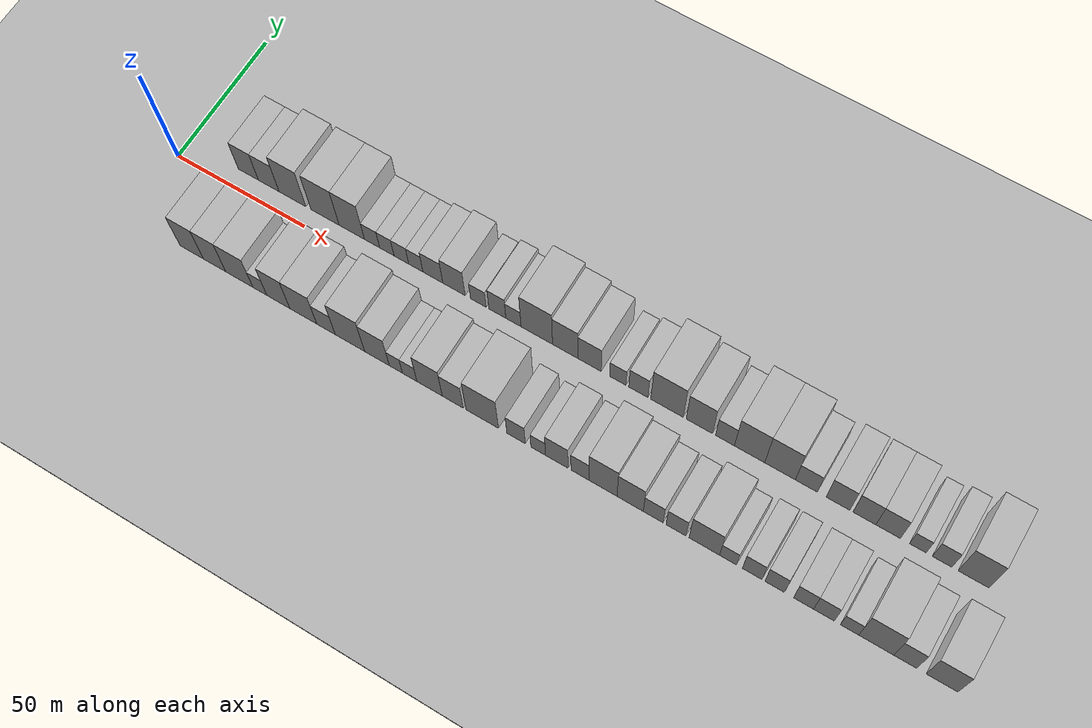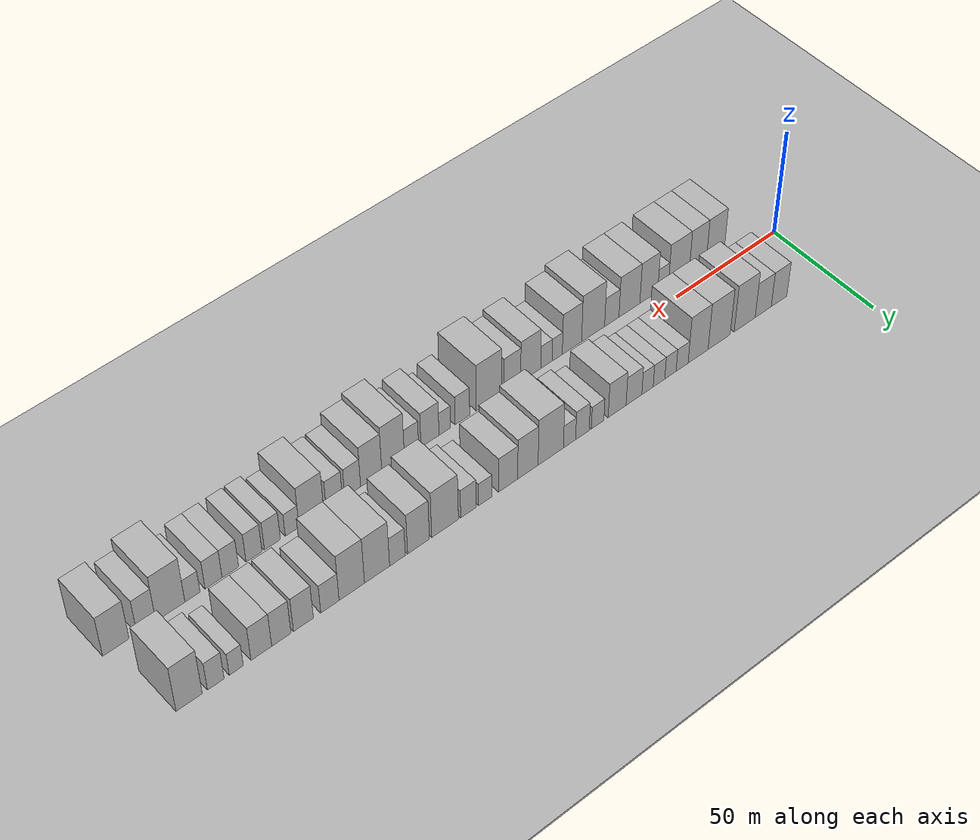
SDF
<?xml version="1.0" encoding="utf-8"?>

<sdf version="1.6">

   <world name="default">

      <gui fullscreen="0">

         <camera name="user_camera">

            <pose>-15 0 4.57585 0 0 0</pose>

            <view_controller>orbit</view_controller>

         </camera>

      </gui>

      <scene>

         <sky>

           <clouds>

             <speed>12</speed>

           </clouds>

         </sky>

         <ambient>0.4 0.4 0.4 1</ambient>

         <background>0.7 0.7 0.7 1</background>

         <shadows>1</shadows>

      </scene>

      <gravity>0 0 -9.8066</gravity>

      <magnetic_field>6e-06 2.3e-05 -4.2e-05</magnetic_field>

      <physics default="0" name="default_physics" type="ode">

         <ode>

            <solver>

               <type>quick</type>

               <iters>10</iters>

               <sor>1.0</sor>

               <use_dynamic_moi_rescaling>0</use_dynamic_moi_rescaling>

            </solver>

            <constraints>

               <cfm>0</cfm>

               <erp>0.2</erp>

               <contact_max_correcting_vel>100</contact_max_correcting_vel>

               <contact_surface_layer>0.001</contact_surface_layer>

            </constraints>

         </ode>

         <max_step_size>0.004</max_step_size>

         <real_time_factor>1</real_time_factor>

         <real_time_update_rate>250</real_time_update_rate>

      </physics>

      <light name="sun" type="directional">

         <cast_shadows>1</cast_shadows>

         <pose>0 0 10 0 0 0</pose>

         <diffuse>0.8 0.8 0.8 1</diffuse>

         <specular>0.2 0.2 0.2 1</specular>

         <attenuation>

            <range>1000</range>

            <constant>0.9</constant>

            <linear>0.01</linear>

            <quadratic>0.001</quadratic>

         </attenuation>

         <direction>-0.5 0.1 -0.9</direction>

      </light>

      <include>

         <name>ground_plane_1</name>

         <uri>model://HANNAS_ground_plane</uri>

         <pose>0 0 0  0 0 0</pose>

      </include>

      <include>

         <name>ground_plane_2</name>

         <uri>model://HANNAS_ground_plane</uri>

         <pose>100 0 0  0 0 0</pose>

      </include>

      <model name="building_1">

         <static>1</static>

         <pose frame="">23.9897 16.0000 0 0.000000 0.000000 1.570796</pose>

         <link name="link">

            <pose frame="">0 0 9.00 0 0 0</pose>

            <collision name="collision">

               <geometry>

                  <box>

                     <size>20.0000 7.9794 18.0000</size>

                  </box>

               </geometry>

               <max_contacts>10</max_contacts>

               <surface>

                  <contact>

                     <ode/>

                  </contact>

                  <bounce/>

                  <friction>

                     <torsional>

                        <ode/>

                     </torsional>

                     <ode/>

                  </friction>

               </surface>

            </collision>

            <visual name="visual">

               <cast_shadows>0</cast_shadows>

               <geometry>

                  <box>

                     <size>20.0000 7.9794 18.0000</size>

                  </box>

               </geometry>

               <material>

                  <script>

                     <uri>model://HANNAS_wall/materials/scripts</uri>

                     <uri>model://HANNAS_wall/materials/textures</uri>

                     <name>vrc/HANNAS_wall</name>

                  </script>

               </material>

            </visual>

            <self_collide>0</self_collide>

            <enable_wind>0</enable_wind>

            <kinematic>0</kinematic>

         </link>

      </model>

      <model name="building_2">

         <static>1</static>

         <pose frame="">32.0457 16.0000 0 0.000000 0.000000 1.570796</pose>

         <link name="link">

            <pose frame="">0 0 9.00 0 0 0</pose>

            <collision name="collision">

               <geometry>

                  <box>

                     <size>20.0000 8.1326 18.0000</size>

                  </box>

               </geometry>

               <max_contacts>10</max_contacts>

               <surface>

                  <contact>

                     <ode/>

                  </contact>

                  <bounce/>

                  <friction>

                     <torsional>

                        <ode/>

                     </torsional>

                     <ode/>

                  </friction>

               </surface>

            </collision>

            <visual name="visual">

               <cast_shadows>0</cast_shadows>

               <geometry>

                  <box>

                     <size>20.0000 8.1326 18.0000</size>

                  </box>

               </geometry>

               <material>

                  <script>

                     <uri>model://HANNAS_wall/materials/scripts</uri>

                     <uri>model://HANNAS_wall/materials/textures</uri>

                     <name>vrc/HANNAS_wall</name>

                  </script>

               </material>

            </visual>

            <self_collide>0</self_collide>

            <enable_wind>0</enable_wind>

            <kinematic>0</kinematic>

         </link>

      </model>

      <model name="building_3">

         <static>1</static>

         <pose frame="">41.3516 16.0000 0 0.000000 0.000000 1.570796</pose>

         <link name="link">

            <pose frame="">0 0 12.00 0 0 0</pose>

            <collision name="collision">

               <geometry>

                  <box>

                     <size>20.0000 10.4791 24.0000</size>

                  </box>

               </geometry>

               <max_contacts>10</max_contacts>

               <surface>

                  <contact>

                     <ode/>

                  </contact>

                  <bounce/>

                  <friction>

                     <torsional>

                        <ode/>

                     </torsional>

                     <ode/>

                  </friction>

               </surface>

            </collision>

            <visual name="visual">

               <cast_shadows>0</cast_shadows>

               <geometry>

                  <box>

                     <size>20.0000 10.4791 24.0000</size>

                  </box>

               </geometry>

               <material>

                  <script>

                     <uri>model://HANNAS_wall/materials/scripts</uri>

                     <uri>model://HANNAS_wall/materials/textures</uri>

                     <name>vrc/HANNAS_wall</name>

                  </script>

               </material>

            </visual>

            <self_collide>0</self_collide>

            <enable_wind>0</enable_wind>

            <kinematic>0</kinematic>

         </link>

      </model>

      <model name="building_4">

         <static>1</static>

         <pose frame="">54.0591 16.0000 0 0.000000 0.000000 1.570796</pose>

         <link name="link">

            <pose frame="">0 0 12.00 0 0 0</pose>

            <collision name="collision">

               <geometry>

                  <box>

                     <size>20.0000 10.9360 24.0000</size>

                  </box>

               </geometry>

               <max_contacts>10</max_contacts>

               <surface>

                  <contact>

                     <ode/>

                  </contact>

                  <bounce/>

                  <friction>

                     <torsional>

                        <ode/>

                     </torsional>

                     <ode/>

                  </friction>

               </surface>

            </collision>

            <visual name="visual">

               <cast_shadows>0</cast_shadows>

               <geometry>

                  <box>

                     <size>20.0000 10.9360 24.0000</size>

                  </box>

               </geometry>

               <material>

                  <script>

                     <uri>model://HANNAS_wall/materials/scripts</uri>

                     <uri>model://HANNAS_wall/materials/textures</uri>

                     <name>vrc/HANNAS_wall</name>

                  </script>

               </material>

            </visual>

            <self_collide>0</self_collide>

            <enable_wind>0</enable_wind>

            <kinematic>0</kinematic>

         </link>

      </model>

      <model name="building_5">

         <static>1</static>

         <pose frame="">64.4099 16.0000 0 0.000000 0.000000 1.570796</pose>

         <link name="link">

            <pose frame="">0 0 12.00 0 0 0</pose>

            <collision name="collision">

               <geometry>

                  <box>

                     <size>20.0000 9.7655 24.0000</size>

                  </box>

               </geometry>

               <max_contacts>10</max_contacts>

               <surface>

                  <contact>

                     <ode/>

                  </contact>

                  <bounce/>

                  <friction>

                     <torsional>

                        <ode/>

                     </torsional>

                     <ode/>

                  </friction>

               </surface>

            </collision>

            <visual name="visual">

               <cast_shadows>0</cast_shadows>

               <geometry>

                  <box>

                     <size>20.0000 9.7655 24.0000</size>

                  </box>

               </geometry>

               <material>

                  <script>

                     <uri>model://HANNAS_wall/materials/scripts</uri>

                     <uri>model://HANNAS_wall/materials/textures</uri>

                     <name>vrc/HANNAS_wall</name>

                  </script>

               </material>

            </visual>

            <self_collide>0</self_collide>

            <enable_wind>0</enable_wind>

            <kinematic>0</kinematic>

         </link>

      </model>

      <model name="building_6">

         <static>1</static>

         <pose frame="">72.1993 16.0000 0 0.000000 0.000000 1.570796</pose>

         <link name="link">

            <pose frame="">0 0 6.00 0 0 0</pose>

            <collision name="collision">

               <geometry>

                  <box>

                     <size>20.0000 5.8133 12.0000</size>

                  </box>

               </geometry>

               <max_contacts>10</max_contacts>

               <surface>

                  <contact>

                     <ode/>

                  </contact>

                  <bounce/>

                  <friction>

                     <torsional>

                        <ode/>

                     </torsional>

                     <ode/>

                  </friction>

               </surface>

            </collision>

            <visual name="visual">

               <cast_shadows>0</cast_shadows>

               <geometry>

                  <box>

                     <size>20.0000 5.8133 12.0000</size>

                  </box>

               </geometry>

               <material>

                  <script>

                     <uri>model://HANNAS_wall/materials/scripts</uri>

                     <uri>model://HANNAS_wall/materials/textures</uri>

                     <name>vrc/HANNAS_wall</name>

                  </script>

               </material>

            </visual>

            <self_collide>0</self_collide>

            <enable_wind>0</enable_wind>

            <kinematic>0</kinematic>

         </link>

      </model>

      <model name="building_7">

         <static>1</static>

         <pose frame="">77.8411 16.0000 0 0.000000 0.000000 1.570796</pose>

         <link name="link">

            <pose frame="">0 0 6.00 0 0 0</pose>

            <collision name="collision">

               <geometry>

                  <box>

                     <size>20.0000 5.4703 12.0000</size>

                  </box>

               </geometry>

               <max_contacts>10</max_contacts>

               <surface>

                  <contact>

                     <ode/>

                  </contact>

                  <bounce/>

                  <friction>

                     <torsional>

                        <ode/>

                     </torsional>

                     <ode/>

                  </friction>

               </surface>

            </collision>

            <visual name="visual">

               <cast_shadows>0</cast_shadows>

               <geometry>

                  <box>

                     <size>20.0000 5.4703 12.0000</size>

                  </box>

               </geometry>

               <material>

                  <script>

                     <uri>model://HANNAS_wall/materials/scripts</uri>

                     <uri>model://HANNAS_wall/materials/textures</uri>

                     <name>vrc/HANNAS_wall</name>

                  </script>

               </material>

            </visual>

            <self_collide>0</self_collide>

            <enable_wind>0</enable_wind>

            <kinematic>0</kinematic>

         </link>

      </model>

      <model name="building_8">

         <static>1</static>

         <pose frame="">83.3580 16.0000 0 0.000000 0.000000 1.570796</pose>

         <link name="link">

            <pose frame="">0 0 6.00 0 0 0</pose>

            <collision name="collision">

               <geometry>

                  <box>

                     <size>20.0000 5.5636 12.0000</size>

                  </box>

               </geometry>

               <max_contacts>10</max_contacts>

               <surface>

                  <contact>

                     <ode/>

                  </contact>

                  <bounce/>

                  <friction>

                     <torsional>

                        <ode/>

                     </torsional>

                     <ode/>

                  </friction>

               </surface>

            </collision>

            <visual name="visual">

               <cast_shadows>0</cast_shadows>

               <geometry>

                  <box>

                     <size>20.0000 5.5636 12.0000</size>

                  </box>

               </geometry>

               <material>

                  <script>

                     <uri>model://HANNAS_wall/materials/scripts</uri>

                     <uri>model://HANNAS_wall/materials/textures</uri>

                     <name>vrc/HANNAS_wall</name>

                  </script>

               </material>

            </visual>

            <self_collide>0</self_collide>

            <enable_wind>0</enable_wind>

            <kinematic>0</kinematic>

         </link>

      </model>

      <model name="building_9">

         <static>1</static>

         <pose frame="">88.8433 16.0000 0 0.000000 0.000000 1.570796</pose>

         <link name="link">

            <pose frame="">0 0 6.00 0 0 0</pose>

            <collision name="collision">

               <geometry>

                  <box>

                     <size>20.0000 5.4069 12.0000</size>

                  </box>

               </geometry>

               <max_contacts>10</max_contacts>

               <surface>

                  <contact>

                     <ode/>

                  </contact>

                  <bounce/>

                  <friction>

                     <torsional>

                        <ode/>

                     </torsional>

                     <ode/>

                  </friction>

               </surface>

            </collision>

            <visual name="visual">

               <cast_shadows>0</cast_shadows>

               <geometry>

                  <box>

                     <size>20.0000 5.4069 12.0000</size>

                  </box>

               </geometry>

               <material>

                  <script>

                     <uri>model://HANNAS_wall/materials/scripts</uri>

                     <uri>model://HANNAS_wall/materials/textures</uri>

                     <name>vrc/HANNAS_wall</name>

                  </script>

               </material>

            </visual>

            <self_collide>0</self_collide>

            <enable_wind>0</enable_wind>

            <kinematic>0</kinematic>

         </link>

      </model>

      <model name="building_10">

         <static>1</static>

         <pose frame="">95.2733 16.0000 0 0.000000 0.000000 1.570796</pose>

         <link name="link">

            <pose frame="">0 0 7.50 0 0 0</pose>

            <collision name="collision">

               <geometry>

                  <box>

                     <size>20.0000 7.4531 15.0000</size>

                  </box>

               </geometry>

               <max_contacts>10</max_contacts>

               <surface>

                  <contact>

                     <ode/>

                  </contact>

                  <bounce/>

                  <friction>

                     <torsional>

                        <ode/>

                     </torsional>

                     <ode/>

                  </friction>

               </surface>

            </collision>

            <visual name="visual">

               <cast_shadows>0</cast_shadows>

               <geometry>

                  <box>

                     <size>20.0000 7.4531 15.0000</size>

                  </box>

               </geometry>

               <material>

                  <script>

                     <uri>model://HANNAS_wall/materials/scripts</uri>

                     <uri>model://HANNAS_wall/materials/textures</uri>

                     <name>vrc/HANNAS_wall</name>

                  </script>

               </material>

            </visual>

            <self_collide>0</self_collide>

            <enable_wind>0</enable_wind>

            <kinematic>0</kinematic>

         </link>

      </model>

      <model name="building_11">

         <static>1</static>

         <pose frame="">103.1877 16.0000 0 0.000000 0.000000 1.570796</pose>

         <link name="link">

            <pose frame="">0 0 9.00 0 0 0</pose>

            <collision name="collision">

               <geometry>

                  <box>

                     <size>20.0000 8.3757 18.0000</size>

                  </box>

               </geometry>

               <max_contacts>10</max_contacts>

               <surface>

                  <contact>

                     <ode/>

                  </contact>

                  <bounce/>

                  <friction>

                     <torsional>

                        <ode/>

                     </torsional>

                     <ode/>

                  </friction>

               </surface>

            </collision>

            <visual name="visual">

               <cast_shadows>0</cast_shadows>

               <geometry>

                  <box>

                     <size>20.0000 8.3757 18.0000</size>

                  </box>

               </geometry>

               <material>

                  <script>

                     <uri>model://HANNAS_wall/materials/scripts</uri>

                     <uri>model://HANNAS_wall/materials/textures</uri>

                     <name>vrc/HANNAS_wall</name>

                  </script>

               </material>

            </visual>

            <self_collide>0</self_collide>

            <enable_wind>0</enable_wind>

            <kinematic>0</kinematic>

         </link>

      </model>

      <model name="building_12">

         <static>1</static>

         <pose frame="">112.2840 16.0000 0 0.000000 0.000000 1.570796</pose>

         <link name="link">

            <pose frame="">0 0 6.00 0 0 0</pose>

            <collision name="collision">

               <geometry>

                  <box>

                     <size>20.0000 5.8167 12.0000</size>

                  </box>

               </geometry>

               <max_contacts>10</max_contacts>

               <surface>

                  <contact>

                     <ode/>

                  </contact>

                  <bounce/>

                  <friction>

                     <torsional>

                        <ode/>

                     </torsional>

                     <ode/>

                  </friction>

               </surface>

            </collision>

            <visual name="visual">

               <cast_shadows>0</cast_shadows>

               <geometry>

                  <box>

                     <size>20.0000 5.8167 12.0000</size>

                  </box>

               </geometry>

               <material>

                  <script>

                     <uri>model://HANNAS_wall/materials/scripts</uri>

                     <uri>model://HANNAS_wall/materials/textures</uri>

                     <name>vrc/HANNAS_wall</name>

                  </script>

               </material>

            </visual>

            <self_collide>0</self_collide>

            <enable_wind>0</enable_wind>

            <kinematic>0</kinematic>

         </link>

      </model>

      <model name="building_13">

         <static>1</static>

         <pose frame="">119.3106 16.0000 0 0.000000 0.000000 1.570796</pose>

         <link name="link">

            <pose frame="">0 0 7.50 0 0 0</pose>

            <collision name="collision">

               <geometry>

                  <box>

                     <size>20.0000 6.2365 15.0000</size>

                  </box>

               </geometry>

               <max_contacts>10</max_contacts>

               <surface>

                  <contact>

                     <ode/>

                  </contact>

                  <bounce/>

                  <friction>

                     <torsional>

                        <ode/>

                     </torsional>

                     <ode/>

                  </friction>

               </surface>

            </collision>

            <visual name="visual">

               <cast_shadows>0</cast_shadows>

               <geometry>

                  <box>

                     <size>20.0000 6.2365 15.0000</size>

                  </box>

               </geometry>

               <material>

                  <script>

                     <uri>model://HANNAS_wall/materials/scripts</uri>

                     <uri>model://HANNAS_wall/materials/textures</uri>

                     <name>vrc/HANNAS_wall</name>

                  </script>

               </material>

            </visual>

            <self_collide>0</self_collide>

            <enable_wind>0</enable_wind>

            <kinematic>0</kinematic>

         </link>

      </model>

      <model name="building_14">

         <static>1</static>

         <pose frame="">125.2256 16.0000 0 0.000000 0.000000 1.570796</pose>

         <link name="link">

            <pose frame="">0 0 6.00 0 0 0</pose>

            <collision name="collision">

               <geometry>

                  <box>

                     <size>20.0000 5.5934 12.0000</size>

                  </box>

               </geometry>

               <max_contacts>10</max_contacts>

               <surface>

                  <contact>

                     <ode/>

                  </contact>

                  <bounce/>

                  <friction>

                     <torsional>

                        <ode/>

                     </torsional>

                     <ode/>

                  </friction>

               </surface>

            </collision>

            <visual name="visual">

               <cast_shadows>0</cast_shadows>

               <geometry>

                  <box>

                     <size>20.0000 5.5934 12.0000</size>

                  </box>

               </geometry>

               <material>

                  <script>

                     <uri>model://HANNAS_wall/materials/scripts</uri>

                     <uri>model://HANNAS_wall/materials/textures</uri>

                     <name>vrc/HANNAS_wall</name>

                  </script>

               </material>

            </visual>

            <self_collide>0</self_collide>

            <enable_wind>0</enable_wind>

            <kinematic>0</kinematic>

         </link>

      </model>

      <model name="building_15">

         <static>1</static>

         <pose frame="">133.7658 16.0000 0 0.000000 0.000000 1.570796</pose>

         <link name="link">

            <pose frame="">0 0 12.00 0 0 0</pose>

            <collision name="collision">

               <geometry>

                  <box>

                     <size>20.0000 11.4869 24.0000</size>

                  </box>

               </geometry>

               <max_contacts>10</max_contacts>

               <surface>

                  <contact>

                     <ode/>

                  </contact>

                  <bounce/>

                  <friction>

                     <torsional>

                        <ode/>

                     </torsional>

                     <ode/>

                  </friction>

               </surface>

            </collision>

            <visual name="visual">

               <cast_shadows>0</cast_shadows>

               <geometry>

                  <box>

                     <size>20.0000 11.4869 24.0000</size>

                  </box>

               </geometry>

               <material>

                  <script>

                     <uri>model://HANNAS_wall/materials/scripts</uri>

                     <uri>model://HANNAS_wall/materials/textures</uri>

                     <name>vrc/HANNAS_wall</name>

                  </script>

               </material>

            </visual>

            <self_collide>0</self_collide>

            <enable_wind>0</enable_wind>

            <kinematic>0</kinematic>

         </link>

      </model>

      <model name="building_16">

         <static>1</static>

         <pose frame="">144.0793 16.0000 0 0.000000 0.000000 1.570796</pose>

         <link name="link">

            <pose frame="">0 0 10.50 0 0 0</pose>

            <collision name="collision">

               <geometry>

                  <box>

                     <size>20.0000 9.1402 21.0000</size>

                  </box>

               </geometry>

               <max_contacts>10</max_contacts>

               <surface>

                  <contact>

                     <ode/>

                  </contact>

                  <bounce/>

                  <friction>

                     <torsional>

                        <ode/>

                     </torsional>

                     <ode/>

                  </friction>

               </surface>

            </collision>

            <visual name="visual">

               <cast_shadows>0</cast_shadows>

               <geometry>

                  <box>

                     <size>20.0000 9.1402 21.0000</size>

                  </box>

               </geometry>

               <material>

                  <script>

                     <uri>model://HANNAS_wall/materials/scripts</uri>

                     <uri>model://HANNAS_wall/materials/textures</uri>

                     <name>vrc/HANNAS_wall</name>

                  </script>

               </material>

            </visual>

            <self_collide>0</self_collide>

            <enable_wind>0</enable_wind>

            <kinematic>0</kinematic>

         </link>

      </model>

      <model name="building_17">

         <static>1</static>

         <pose frame="">152.8760 16.0000 0 0.000000 0.000000 1.570796</pose>

         <link name="link">

            <pose frame="">0 0 9.00 0 0 0</pose>

            <collision name="collision">

               <geometry>

                  <box>

                     <size>20.0000 8.4531 18.0000</size>

                  </box>

               </geometry>

               <max_contacts>10</max_contacts>

               <surface>

                  <contact>

                     <ode/>

                  </contact>

                  <bounce/>

                  <friction>

                     <torsional>

                        <ode/>

                     </torsional>

                     <ode/>

                  </friction>

               </surface>

            </collision>

            <visual name="visual">

               <cast_shadows>0</cast_shadows>

               <geometry>

                  <box>

                     <size>20.0000 8.4531 18.0000</size>

                  </box>

               </geometry>

               <material>

                  <script>

                     <uri>model://HANNAS_wall/materials/scripts</uri>

                     <uri>model://HANNAS_wall/materials/textures</uri>

                     <name>vrc/HANNAS_wall</name>

                  </script>

               </material>

            </visual>

            <self_collide>0</self_collide>

            <enable_wind>0</enable_wind>

            <kinematic>0</kinematic>

         </link>

      </model>

      <model name="building_18">

         <static>1</static>

         <pose frame="">163.0296 16.0000 0 0.000000 0.000000 1.570796</pose>

         <link name="link">

            <pose frame="">0 0 6.00 0 0 0</pose>

            <collision name="collision">

               <geometry>

                  <box>

                     <size>20.0000 5.8539 12.0000</size>

                  </box>

               </geometry>

               <max_contacts>10</max_contacts>

               <surface>

                  <contact>

                     <ode/>

                  </contact>

                  <bounce/>

                  <friction>

                     <torsional>

                        <ode/>

                     </torsional>

                     <ode/>

                  </friction>

               </surface>

            </collision>

            <visual name="visual">

               <cast_shadows>0</cast_shadows>

               <geometry>

                  <box>

                     <size>20.0000 5.8539 12.0000</size>

                  </box>

               </geometry>

               <material>

                  <script>

                     <uri>model://HANNAS_wall/materials/scripts</uri>

                     <uri>model://HANNAS_wall/materials/textures</uri>

                     <name>vrc/HANNAS_wall</name>

                  </script>

               </material>

            </visual>

            <self_collide>0</self_collide>

            <enable_wind>0</enable_wind>

            <kinematic>0</kinematic>

         </link>

      </model>

      <model name="building_19">

         <static>1</static>

         <pose frame="">170.3531 16.0000 0 0.000000 0.000000 1.570796</pose>

         <link name="link">

            <pose frame="">0 0 7.50 0 0 0</pose>

            <collision name="collision">

               <geometry>

                  <box>

                     <size>20.0000 6.7931 15.0000</size>

                  </box>

               </geometry>

               <max_contacts>10</max_contacts>

               <surface>

                  <contact>

                     <ode/>

                  </contact>

                  <bounce/>

                  <friction>

                     <torsional>

                        <ode/>

                     </torsional>

                     <ode/>

                  </friction>

               </surface>

            </collision>

            <visual name="visual">

               <cast_shadows>0</cast_shadows>

               <geometry>

                  <box>

                     <size>20.0000 6.7931 15.0000</size>

                  </box>

               </geometry>

               <material>

                  <script>

                     <uri>model://HANNAS_wall/materials/scripts</uri>

                     <uri>model://HANNAS_wall/materials/textures</uri>

                     <name>vrc/HANNAS_wall</name>

                  </script>

               </material>

            </visual>

            <self_collide>0</self_collide>

            <enable_wind>0</enable_wind>

            <kinematic>0</kinematic>

         </link>

      </model>

      <model name="building_20">

         <static>1</static>

         <pose frame="">180.4915 16.0000 0 0.000000 0.000000 1.570796</pose>

         <link name="link">

            <pose frame="">0 0 12.00 0 0 0</pose>

            <collision name="collision">

               <geometry>

                  <box>

                     <size>20.0000 11.4838 24.0000</size>

                  </box>

               </geometry>

               <max_contacts>10</max_contacts>

               <surface>

                  <contact>

                     <ode/>

                  </contact>

                  <bounce/>

                  <friction>

                     <torsional>

                        <ode/>

                     </torsional>

                     <ode/>

                  </friction>

               </surface>

            </collision>

            <visual name="visual">

               <cast_shadows>0</cast_shadows>

               <geometry>

                  <box>

                     <size>20.0000 11.4838 24.0000</size>

                  </box>

               </geometry>

               <material>

                  <script>

                     <uri>model://HANNAS_wall/materials/scripts</uri>

                     <uri>model://HANNAS_wall/materials/textures</uri>

                     <name>vrc/HANNAS_wall</name>

                  </script>

               </material>

            </visual>

            <self_collide>0</self_collide>

            <enable_wind>0</enable_wind>

            <kinematic>0</kinematic>

         </link>

      </model>

      <model name="building_21">

         <static>1</static>

         <pose frame="">191.8626 16.0000 0 0.000000 0.000000 1.570796</pose>

         <link name="link">

            <pose frame="">0 0 10.50 0 0 0</pose>

            <collision name="collision">

               <geometry>

                  <box>

                     <size>20.0000 9.2583 21.0000</size>

                  </box>

               </geometry>

               <max_contacts>10</max_contacts>

               <surface>

                  <contact>

                     <ode/>

                  </contact>

                  <bounce/>

                  <friction>

                     <torsional>

                        <ode/>

                     </torsional>

                     <ode/>

                  </friction>

               </surface>

            </collision>

            <visual name="visual">

               <cast_shadows>0</cast_shadows>

               <geometry>

                  <box>

                     <size>20.0000 9.2583 21.0000</size>

                  </box>

               </geometry>

               <material>

                  <script>

                     <uri>model://HANNAS_wall/materials/scripts</uri>

                     <uri>model://HANNAS_wall/materials/textures</uri>

                     <name>vrc/HANNAS_wall</name>

                  </script>

               </material>

            </visual>

            <self_collide>0</self_collide>

            <enable_wind>0</enable_wind>

            <kinematic>0</kinematic>

         </link>

      </model>

      <model name="building_22">

         <static>1</static>

         <pose frame="">200.7845 16.0000 0 0.000000 0.000000 1.570796</pose>

         <link name="link">

            <pose frame="">0 0 7.50 0 0 0</pose>

            <collision name="collision">

               <geometry>

                  <box>

                     <size>20.0000 6.5855 15.0000</size>

                  </box>

               </geometry>

               <max_contacts>10</max_contacts>

               <surface>

                  <contact>

                     <ode/>

                  </contact>

                  <bounce/>

                  <friction>

                     <torsional>

                        <ode/>

                     </torsional>

                     <ode/>

                  </friction>

               </surface>

            </collision>

            <visual name="visual">

               <cast_shadows>0</cast_shadows>

               <geometry>

                  <box>

                     <size>20.0000 6.5855 15.0000</size>

                  </box>

               </geometry>

               <material>

                  <script>

                     <uri>model://HANNAS_wall/materials/scripts</uri>

                     <uri>model://HANNAS_wall/materials/textures</uri>

                     <name>vrc/HANNAS_wall</name>

                  </script>

               </material>

            </visual>

            <self_collide>0</self_collide>

            <enable_wind>0</enable_wind>

            <kinematic>0</kinematic>

         </link>

      </model>

      <model name="building_23">

         <static>1</static>

         <pose frame="">209.3078 16.0000 0 0.000000 0.000000 1.570796</pose>

         <link name="link">

            <pose frame="">0 0 12.00 0 0 0</pose>

            <collision name="collision">

               <geometry>

                  <box>

                     <size>20.0000 10.4612 24.0000</size>

                  </box>

               </geometry>

               <max_contacts>10</max_contacts>

               <surface>

                  <contact>

                     <ode/>

                  </contact>

                  <bounce/>

                  <friction>

                     <torsional>

                        <ode/>

                     </torsional>

                     <ode/>

                  </friction>

               </surface>

            </collision>

            <visual name="visual">

               <cast_shadows>0</cast_shadows>

               <geometry>

                  <box>

                     <size>20.0000 10.4612 24.0000</size>

                  </box>

               </geometry>

               <material>

                  <script>

                     <uri>model://HANNAS_wall/materials/scripts</uri>

                     <uri>model://HANNAS_wall/materials/textures</uri>

                     <name>vrc/HANNAS_wall</name>

                  </script>

               </material>

            </visual>

            <self_collide>0</self_collide>

            <enable_wind>0</enable_wind>

            <kinematic>0</kinematic>

         </link>

      </model>

      <model name="building_24">

         <static>1</static>

         <pose frame="">219.7901 16.0000 0 0.000000 0.000000 1.570796</pose>

         <link name="link">

            <pose frame="">0 0 12.00 0 0 0</pose>

            <collision name="collision">

               <geometry>

                  <box>

                     <size>20.0000 10.5034 24.0000</size>

                  </box>

               </geometry>

               <max_contacts>10</max_contacts>

               <surface>

                  <contact>

                     <ode/>

                  </contact>

                  <bounce/>

                  <friction>

                     <torsional>

                        <ode/>

                     </torsional>

                     <ode/>

                  </friction>

               </surface>

            </collision>

            <visual name="visual">

               <cast_shadows>0</cast_shadows>

               <geometry>

                  <box>

                     <size>20.0000 10.5034 24.0000</size>

                  </box>

               </geometry>

               <material>

                  <script>

                     <uri>model://HANNAS_wall/materials/scripts</uri>

                     <uri>model://HANNAS_wall/materials/textures</uri>

                     <name>vrc/HANNAS_wall</name>

                  </script>

               </material>

            </visual>

            <self_collide>0</self_collide>

            <enable_wind>0</enable_wind>

            <kinematic>0</kinematic>

         </link>

      </model>

      <model name="building_25">

         <static>1</static>

         <pose frame="">228.7678 16.0000 0 0.000000 0.000000 1.570796</pose>

         <link name="link">

            <pose frame="">0 0 7.50 0 0 0</pose>

            <collision name="collision">

               <geometry>

                  <box>

                     <size>20.0000 7.4520 15.0000</size>

                  </box>

               </geometry>

               <max_contacts>10</max_contacts>

               <surface>

                  <contact>

                     <ode/>

                  </contact>

                  <bounce/>

                  <friction>

                     <torsional>

                        <ode/>

                     </torsional>

                     <ode/>

                  </friction>

               </surface>

            </collision>

            <visual name="visual">

               <cast_shadows>0</cast_shadows>

               <geometry>

                  <box>

                     <size>20.0000 7.4520 15.0000</size>

                  </box>

               </geometry>

               <material>

                  <script>

                     <uri>model://HANNAS_wall/materials/scripts</uri>

                     <uri>model://HANNAS_wall/materials/textures</uri>

                     <name>vrc/HANNAS_wall</name>

                  </script>

               </material>

            </visual>

            <self_collide>0</self_collide>

            <enable_wind>0</enable_wind>

            <kinematic>0</kinematic>

         </link>

      </model>

      <model name="building_26">

         <static>1</static>

         <pose frame="">239.5030 16.0000 0 0.000000 0.000000 1.570796</pose>

         <link name="link">

            <pose frame="">0 0 9.00 0 0 0</pose>

            <collision name="collision">

               <geometry>

                  <box>

                     <size>20.0000 8.0183 18.0000</size>

                  </box>

               </geometry>

               <max_contacts>10</max_contacts>

               <surface>

                  <contact>

                     <ode/>

                  </contact>

                  <bounce/>

                  <friction>

                     <torsional>

                        <ode/>

                     </torsional>

                     <ode/>

                  </friction>

               </surface>

            </collision>

            <visual name="visual">

               <cast_shadows>0</cast_shadows>

               <geometry>

                  <box>

                     <size>20.0000 8.0183 18.0000</size>

                  </box>

               </geometry>

               <material>

                  <script>

                     <uri>model://HANNAS_wall/materials/scripts</uri>

                     <uri>model://HANNAS_wall/materials/textures</uri>

                     <name>vrc/HANNAS_wall</name>

                  </script>

               </material>

            </visual>

            <self_collide>0</self_collide>

            <enable_wind>0</enable_wind>

            <kinematic>0</kinematic>

         </link>

      </model>

      <model name="building_27">

         <static>1</static>

         <pose frame="">248.3474 16.0000 0 0.000000 0.000000 1.570796</pose>

         <link name="link">

            <pose frame="">0 0 9.00 0 0 0</pose>

            <collision name="collision">

               <geometry>

                  <box>

                     <size>20.0000 7.6706 18.0000</size>

                  </box>

               </geometry>

               <max_contacts>10</max_contacts>

               <surface>

                  <contact>

                     <ode/>

                  </contact>

                  <bounce/>

                  <friction>

                     <torsional>

                        <ode/>

                     </torsional>

                     <ode/>

                  </friction>

               </surface>

            </collision>

            <visual name="visual">

               <cast_shadows>0</cast_shadows>

               <geometry>

                  <box>

                     <size>20.0000 7.6706 18.0000</size>

                  </box>

               </geometry>

               <material>

                  <script>

                     <uri>model://HANNAS_wall/materials/scripts</uri>

                     <uri>model://HANNAS_wall/materials/textures</uri>

                     <name>vrc/HANNAS_wall</name>

                  </script>

               </material>

            </visual>

            <self_collide>0</self_collide>

            <enable_wind>0</enable_wind>

            <kinematic>0</kinematic>

         </link>

      </model>

      <model name="building_28">

         <static>1</static>

         <pose frame="">256.2662 16.0000 0 0.000000 0.000000 1.570796</pose>

         <link name="link">

            <pose frame="">0 0 9.00 0 0 0</pose>

            <collision name="collision">

               <geometry>

                  <box>

                     <size>20.0000 8.1670 18.0000</size>

                  </box>

               </geometry>

               <max_contacts>10</max_contacts>

               <surface>

                  <contact>

                     <ode/>

                  </contact>

                  <bounce/>

                  <friction>

                     <torsional>

                        <ode/>

                     </torsional>

                     <ode/>

                  </friction>

               </surface>

            </collision>

            <visual name="visual">

               <cast_shadows>0</cast_shadows>

               <geometry>

                  <box>

                     <size>20.0000 8.1670 18.0000</size>

                  </box>

               </geometry>

               <material>

                  <script>

                     <uri>model://HANNAS_wall/materials/scripts</uri>

                     <uri>model://HANNAS_wall/materials/textures</uri>

                     <name>vrc/HANNAS_wall</name>

                  </script>

               </material>

            </visual>

            <self_collide>0</self_collide>

            <enable_wind>0</enable_wind>

            <kinematic>0</kinematic>

         </link>

      </model>

      <model name="building_29">

         <static>1</static>

         <pose frame="">266.1053 16.0000 0 0.000000 0.000000 1.570796</pose>

         <link name="link">

            <pose frame="">0 0 6.00 0 0 0</pose>

            <collision name="collision">

               <geometry>

                  <box>

                     <size>20.0000 5.5113 12.0000</size>

                  </box>

               </geometry>

               <max_contacts>10</max_contacts>

               <surface>

                  <contact>

                     <ode/>

                  </contact>

                  <bounce/>

                  <friction>

                     <torsional>

                        <ode/>

                     </torsional>

                     <ode/>

                  </friction>

               </surface>

            </collision>

            <visual name="visual">

               <cast_shadows>0</cast_shadows>

               <geometry>

                  <box>

                     <size>20.0000 5.5113 12.0000</size>

                  </box>

               </geometry>

               <material>

                  <script>

                     <uri>model://HANNAS_wall/materials/scripts</uri>

                     <uri>model://HANNAS_wall/materials/textures</uri>

                     <name>vrc/HANNAS_wall</name>

                  </script>

               </material>

            </visual>

            <self_collide>0</self_collide>

            <enable_wind>0</enable_wind>

            <kinematic>0</kinematic>

         </link>

      </model>

      <model name="building_30">

         <static>1</static>

         <pose frame="">274.0847 16.0000 0 0.000000 0.000000 1.570796</pose>

         <link name="link">

            <pose frame="">0 0 7.50 0 0 0</pose>

            <collision name="collision">

               <geometry>

                  <box>

                     <size>20.0000 6.4473 15.0000</size>

                  </box>

               </geometry>

               <max_contacts>10</max_contacts>

               <surface>

                  <contact>

                     <ode/>

                  </contact>

                  <bounce/>

                  <friction>

                     <torsional>

                        <ode/>

                     </torsional>

                     <ode/>

                  </friction>

               </surface>

            </collision>

            <visual name="visual">

               <cast_shadows>0</cast_shadows>

               <geometry>

                  <box>

                     <size>20.0000 6.4473 15.0000</size>

                  </box>

               </geometry>

               <material>

                  <script>

                     <uri>model://HANNAS_wall/materials/scripts</uri>

                     <uri>model://HANNAS_wall/materials/textures</uri>

                     <name>vrc/HANNAS_wall</name>

                  </script>

               </material>

            </visual>

            <self_collide>0</self_collide>

            <enable_wind>0</enable_wind>

            <kinematic>0</kinematic>

         </link>

      </model>

      <model name="building_31">

         <static>1</static>

         <pose frame="">284.3253 16.0000 0 0.000000 0.000000 1.570796</pose>

         <link name="link">

            <pose frame="">0 0 12.00 0 0 0</pose>

            <collision name="collision">

               <geometry>

                  <box>

                     <size>20.0000 10.0339 24.0000</size>

                  </box>

               </geometry>

               <max_contacts>10</max_contacts>

               <surface>

                  <contact>

                     <ode/>

                  </contact>

                  <bounce/>

                  <friction>

                     <torsional>

                        <ode/>

                     </torsional>

                     <ode/>

                  </friction>

               </surface>

            </collision>

            <visual name="visual">

               <cast_shadows>0</cast_shadows>

               <geometry>

                  <box>

                     <size>20.0000 10.0339 24.0000</size>

                  </box>

               </geometry>

               <material>

                  <script>

                     <uri>model://HANNAS_wall/materials/scripts</uri>

                     <uri>model://HANNAS_wall/materials/textures</uri>

                     <name>vrc/HANNAS_wall</name>

                  </script>

               </material>

            </visual>

            <self_collide>0</self_collide>

            <enable_wind>0</enable_wind>

            <kinematic>0</kinematic>

         </link>

      </model>

      <model name="building_32">

         <static>1</static>

         <pose frame="">24.6128 -16.0000 0 0.000000 0.000000 1.570796</pose>

         <link name="link">

            <pose frame="">0 0 10.50 0 0 0</pose>

            <collision name="collision">

               <geometry>

                  <box>

                     <size>20.0000 9.2257 21.0000</size>

                  </box>

               </geometry>

               <max_contacts>10</max_contacts>

               <surface>

                  <contact>

                     <ode/>

                  </contact>

                  <bounce/>

                  <friction>

                     <torsional>

                        <ode/>

                     </torsional>

                     <ode/>

                  </friction>

               </surface>

            </collision>

            <visual name="visual">

               <cast_shadows>0</cast_shadows>

               <geometry>

                  <box>

                     <size>20.0000 9.2257 21.0000</size>

                  </box>

               </geometry>

               <material>

                  <script>

                     <uri>model://HANNAS_wall/materials/scripts</uri>

                     <uri>model://HANNAS_wall/materials/textures</uri>

                     <name>vrc/HANNAS_wall</name>

                  </script>

               </material>

            </visual>

            <self_collide>0</self_collide>

            <enable_wind>0</enable_wind>

            <kinematic>0</kinematic>

         </link>

      </model>

      <model name="building_33">

         <static>1</static>

         <pose frame="">33.5681 -16.0000 0 0.000000 0.000000 1.570796</pose>

         <link name="link">

            <pose frame="">0 0 10.50 0 0 0</pose>

            <collision name="collision">

               <geometry>

                  <box>

                     <size>20.0000 8.6849 21.0000</size>

                  </box>

               </geometry>

               <max_contacts>10</max_contacts>

               <surface>

                  <contact>

                     <ode/>

                  </contact>

                  <bounce/>

                  <friction>

                     <torsional>

                        <ode/>

                     </torsional>

                     <ode/>

                  </friction>

               </surface>

            </collision>

            <visual name="visual">

               <cast_shadows>0</cast_shadows>

               <geometry>

                  <box>

                     <size>20.0000 8.6849 21.0000</size>

                  </box>

               </geometry>

               <material>

                  <script>

                     <uri>model://HANNAS_wall/materials/scripts</uri>

                     <uri>model://HANNAS_wall/materials/textures</uri>

                     <name>vrc/HANNAS_wall</name>

                  </script>

               </material>

            </visual>

            <self_collide>0</self_collide>

            <enable_wind>0</enable_wind>

            <kinematic>0</kinematic>

         </link>

      </model>

      <model name="building_34">

         <static>1</static>

         <pose frame="">43.1339 -16.0000 0 0.000000 0.000000 1.570796</pose>

         <link name="link">

            <pose frame="">0 0 10.50 0 0 0</pose>

            <collision name="collision">

               <geometry>

                  <box>

                     <size>20.0000 10.4465 21.0000</size>

                  </box>

               </geometry>

               <max_contacts>10</max_contacts>

               <surface>

                  <contact>

                     <ode/>

                  </contact>

                  <bounce/>

                  <friction>

                     <torsional>

                        <ode/>

                     </torsional>

                     <ode/>

                  </friction>

               </surface>

            </collision>

            <visual name="visual">

               <cast_shadows>0</cast_shadows>

               <geometry>

                  <box>

                     <size>20.0000 10.4465 21.0000</size>

                  </box>

               </geometry>

               <material>

                  <script>

                     <uri>model://HANNAS_wall/materials/scripts</uri>

                     <uri>model://HANNAS_wall/materials/textures</uri>

                     <name>vrc/HANNAS_wall</name>

                  </script>

               </material>

            </visual>

            <self_collide>0</self_collide>

            <enable_wind>0</enable_wind>

            <kinematic>0</kinematic>

         </link>

      </model>

      <model name="building_35">

         <static>1</static>

         <pose frame="">51.0194 -16.0000 0 0.000000 0.000000 1.570796</pose>

         <link name="link">

            <pose frame="">0 0 6.00 0 0 0</pose>

            <collision name="collision">

               <geometry>

                  <box>

                     <size>20.0000 5.3245 12.0000</size>

                  </box>

               </geometry>

               <max_contacts>10</max_contacts>

               <surface>

                  <contact>

                     <ode/>

                  </contact>

                  <bounce/>

                  <friction>

                     <torsional>

                        <ode/>

                     </torsional>

                     <ode/>

                  </friction>

               </surface>

            </collision>

            <visual name="visual">

               <cast_shadows>0</cast_shadows>

               <geometry>

                  <box>

                     <size>20.0000 5.3245 12.0000</size>

                  </box>

               </geometry>

               <material>

                  <script>

                     <uri>model://HANNAS_wall/materials/scripts</uri>

                     <uri>model://HANNAS_wall/materials/textures</uri>

                     <name>vrc/HANNAS_wall</name>

                  </script>

               </material>

            </visual>

            <self_collide>0</self_collide>

            <enable_wind>0</enable_wind>

            <kinematic>0</kinematic>

         </link>

      </model>

      <model name="building_36">

         <static>1</static>

         <pose frame="">58.0935 -16.0000 0 0.000000 0.000000 1.570796</pose>

         <link name="link">

            <pose frame="">0 0 10.50 0 0 0</pose>

            <collision name="collision">

               <geometry>

                  <box>

                     <size>20.0000 8.8238 21.0000</size>

                  </box>

               </geometry>

               <max_contacts>10</max_contacts>

               <surface>

                  <contact>

                     <ode/>

                  </contact>

                  <bounce/>

                  <friction>

                     <torsional>

                        <ode/>

                     </torsional>

                     <ode/>

                  </friction>

               </surface>

            </collision>

            <visual name="visual">

               <cast_shadows>0</cast_shadows>

               <geometry>

                  <box>

                     <size>20.0000 8.8238 21.0000</size>

                  </box>

               </geometry>

               <material>

                  <script>

                     <uri>model://HANNAS_wall/materials/scripts</uri>

                     <uri>model://HANNAS_wall/materials/textures</uri>

                     <name>vrc/HANNAS_wall</name>

                  </script>

               </material>

            </visual>

            <self_collide>0</self_collide>

            <enable_wind>0</enable_wind>

            <kinematic>0</kinematic>

         </link>

      </model>

      <model name="building_37">

         <static>1</static>

         <pose frame="">67.6104 -16.0000 0 0.000000 0.000000 1.570796</pose>

         <link name="link">

            <pose frame="">0 0 10.50 0 0 0</pose>

            <collision name="collision">

               <geometry>

                  <box>

                     <size>20.0000 10.2100 21.0000</size>

                  </box>

               </geometry>

               <max_contacts>10</max_contacts>

               <surface>

                  <contact>

                     <ode/>

                  </contact>

                  <bounce/>

                  <friction>

                     <torsional>

                        <ode/>

                     </torsional>

                     <ode/>

                  </friction>

               </surface>

            </collision>

            <visual name="visual">

               <cast_shadows>0</cast_shadows>

               <geometry>

                  <box>

                     <size>20.0000 10.2100 21.0000</size>

                  </box>

               </geometry>

               <material>

                  <script>

                     <uri>model://HANNAS_wall/materials/scripts</uri>

                     <uri>model://HANNAS_wall/materials/textures</uri>

                     <name>vrc/HANNAS_wall</name>

                  </script>

               </material>

            </visual>

            <self_collide>0</self_collide>

            <enable_wind>0</enable_wind>

            <kinematic>0</kinematic>

         </link>

      </model>

      <model name="building_38">

         <static>1</static>

         <pose frame="">76.1924 -16.0000 0 0.000000 0.000000 1.570796</pose>

         <link name="link">

            <pose frame="">0 0 7.50 0 0 0</pose>

            <collision name="collision">

               <geometry>

                  <box>

                     <size>20.0000 6.9540 15.0000</size>

                  </box>

               </geometry>

               <max_contacts>10</max_contacts>

               <surface>

                  <contact>

                     <ode/>

                  </contact>

                  <bounce/>

                  <friction>

                     <torsional>

                        <ode/>

                     </torsional>

                     <ode/>

                  </friction>

               </surface>

            </collision>

            <visual name="visual">

               <cast_shadows>0</cast_shadows>

               <geometry>

                  <box>

                     <size>20.0000 6.9540 15.0000</size>

                  </box>

               </geometry>

               <material>

                  <script>

                     <uri>model://HANNAS_wall/materials/scripts</uri>

                     <uri>model://HANNAS_wall/materials/textures</uri>

                     <name>vrc/HANNAS_wall</name>

                  </script>

               </material>

            </visual>

            <self_collide>0</self_collide>

            <enable_wind>0</enable_wind>

            <kinematic>0</kinematic>

         </link>

      </model>

      <model name="building_39">

         <static>1</static>

         <pose frame="">85.1978 -16.0000 0 0.000000 0.000000 1.570796</pose>

         <link name="link">

            <pose frame="">0 0 12.00 0 0 0</pose>

            <collision name="collision">

               <geometry>

                  <box>

                     <size>20.0000 11.0569 24.0000</size>

                  </box>

               </geometry>

               <max_contacts>10</max_contacts>

               <surface>

                  <contact>

                     <ode/>

                  </contact>

                  <bounce/>

                  <friction>

                     <torsional>

                        <ode/>

                     </torsional>

                     <ode/>

                  </friction>

               </surface>

            </collision>

            <visual name="visual">

               <cast_shadows>0</cast_shadows>

               <geometry>

                  <box>

                     <size>20.0000 11.0569 24.0000</size>

                  </box>

               </geometry>

               <material>

                  <script>

                     <uri>model://HANNAS_wall/materials/scripts</uri>

                     <uri>model://HANNAS_wall/materials/textures</uri>

                     <name>vrc/HANNAS_wall</name>

                  </script>

               </material>

            </visual>

            <self_collide>0</self_collide>

            <enable_wind>0</enable_wind>

            <kinematic>0</kinematic>

         </link>

      </model>

      <model name="building_40">

         <static>1</static>

         <pose frame="">95.2963 -16.0000 0 0.000000 0.000000 1.570796</pose>

         <link name="link">

            <pose frame="">0 0 10.50 0 0 0</pose>

            <collision name="collision">

               <geometry>

                  <box>

                     <size>20.0000 9.1401 21.0000</size>

                  </box>

               </geometry>

               <max_contacts>10</max_contacts>

               <surface>

                  <contact>

                     <ode/>

                  </contact>

                  <bounce/>

                  <friction>

                     <torsional>

                        <ode/>

                     </torsional>

                     <ode/>

                  </friction>

               </surface>

            </collision>

            <visual name="visual">

               <cast_shadows>0</cast_shadows>

               <geometry>

                  <box>

                     <size>20.0000 9.1401 21.0000</size>

                  </box>

               </geometry>

               <material>

                  <script>

                     <uri>model://HANNAS_wall/materials/scripts</uri>

                     <uri>model://HANNAS_wall/materials/textures</uri>

                     <name>vrc/HANNAS_wall</name>

                  </script>

               </material>

            </visual>

            <self_collide>0</self_collide>

            <enable_wind>0</enable_wind>

            <kinematic>0</kinematic>

         </link>

      </model>

      <model name="building_41">

         <static>1</static>

         <pose frame="">102.2779 -16.0000 0 0.000000 0.000000 1.570796</pose>

         <link name="link">

            <pose frame="">0 0 6.00 0 0 0</pose>

            <collision name="collision">

               <geometry>

                  <box>

                     <size>20.0000 4.8230 12.0000</size>

                  </box>

               </geometry>

               <max_contacts>10</max_contacts>

               <surface>

                  <contact>

                     <ode/>

                  </contact>

                  <bounce/>

                  <friction>

                     <torsional>

                        <ode/>

                     </torsional>

                     <ode/>

                  </friction>

               </surface>

            </collision>

            <visual name="visual">

               <cast_shadows>0</cast_shadows>

               <geometry>

                  <box>

                     <size>20.0000 4.8230 12.0000</size>

                  </box>

               </geometry>

               <material>

                  <script>

                     <uri>model://HANNAS_wall/materials/scripts</uri>

                     <uri>model://HANNAS_wall/materials/textures</uri>

                     <name>vrc/HANNAS_wall</name>

                  </script>

               </material>

            </visual>

            <self_collide>0</self_collide>

            <enable_wind>0</enable_wind>

            <kinematic>0</kinematic>

         </link>

      </model>

      <model name="building_42">

         <static>1</static>

         <pose frame="">107.3566 -16.0000 0 0.000000 0.000000 1.570796</pose>

         <link name="link">

            <pose frame="">0 0 6.00 0 0 0</pose>

            <collision name="collision">

               <geometry>

                  <box>

                     <size>20.0000 5.3344 12.0000</size>

                  </box>

               </geometry>

               <max_contacts>10</max_contacts>

               <surface>

                  <contact>

                     <ode/>

                  </contact>

                  <bounce/>

                  <friction>

                     <torsional>

                        <ode/>

                     </torsional>

                     <ode/>

                  </friction>

               </surface>

            </collision>

            <visual name="visual">

               <cast_shadows>0</cast_shadows>

               <geometry>

                  <box>

                     <size>20.0000 5.3344 12.0000</size>

                  </box>

               </geometry>

               <material>

                  <script>

                     <uri>model://HANNAS_wall/materials/scripts</uri>

                     <uri>model://HANNAS_wall/materials/textures</uri>

                     <name>vrc/HANNAS_wall</name>

                  </script>

               </material>

            </visual>

            <self_collide>0</self_collide>

            <enable_wind>0</enable_wind>

            <kinematic>0</kinematic>

         </link>

      </model>

      <model name="building_43">

         <static>1</static>

         <pose frame="">114.6691 -16.0000 0 0.000000 0.000000 1.570796</pose>

         <link name="link">

            <pose frame="">0 0 10.50 0 0 0</pose>

            <collision name="collision">

               <geometry>

                  <box>

                     <size>20.0000 9.2907 21.0000</size>

                  </box>

               </geometry>

               <max_contacts>10</max_contacts>

               <surface>

                  <contact>

                     <ode/>

                  </contact>

                  <bounce/>

                  <friction>

                     <torsional>

                        <ode/>

                     </torsional>

                     <ode/>

                  </friction>

               </surface>

            </collision>

            <visual name="visual">

               <cast_shadows>0</cast_shadows>

               <geometry>

                  <box>

                     <size>20.0000 9.2907 21.0000</size>

                  </box>

               </geometry>

               <material>

                  <script>

                     <uri>model://HANNAS_wall/materials/scripts</uri>

                     <uri>model://HANNAS_wall/materials/textures</uri>

                     <name>vrc/HANNAS_wall</name>

                  </script>

               </material>

            </visual>

            <self_collide>0</self_collide>

            <enable_wind>0</enable_wind>

            <kinematic>0</kinematic>

         </link>

      </model>

      <model name="building_44">

         <static>1</static>

         <pose frame="">123.1195 -16.0000 0 0.000000 0.000000 1.570796</pose>

         <link name="link">

            <pose frame="">0 0 9.00 0 0 0</pose>

            <collision name="collision">

               <geometry>

                  <box>

                     <size>20.0000 7.6099 18.0000</size>

                  </box>

               </geometry>

               <max_contacts>10</max_contacts>

               <surface>

                  <contact>

                     <ode/>

                  </contact>

                  <bounce/>

                  <friction>

                     <torsional>

                        <ode/>

                     </torsional>

                     <ode/>

                  </friction>

               </surface>

            </collision>

            <visual name="visual">

               <cast_shadows>0</cast_shadows>

               <geometry>

                  <box>

                     <size>20.0000 7.6099 18.0000</size>

                  </box>

               </geometry>

               <material>

                  <script>

                     <uri>model://HANNAS_wall/materials/scripts</uri>

                     <uri>model://HANNAS_wall/materials/textures</uri>

                     <name>vrc/HANNAS_wall</name>

                  </script>

               </material>

            </visual>

            <self_collide>0</self_collide>

            <enable_wind>0</enable_wind>

            <kinematic>0</kinematic>

         </link>

      </model>

      <model name="building_45">

         <static>1</static>

         <pose frame="">133.7897 -16.0000 0 0.000000 0.000000 1.570796</pose>

         <link name="link">

            <pose frame="">0 0 12.00 0 0 0</pose>

            <collision name="collision">

               <geometry>

                  <box>

                     <size>20.0000 11.7305 24.0000</size>

                  </box>

               </geometry>

               <max_contacts>10</max_contacts>

               <surface>

                  <contact>

                     <ode/>

                  </contact>

                  <bounce/>

                  <friction>

                     <torsional>

                        <ode/>

                     </torsional>

                     <ode/>

                  </friction>

               </surface>

            </collision>

            <visual name="visual">

               <cast_shadows>0</cast_shadows>

               <geometry>

                  <box>

                     <size>20.0000 11.7305 24.0000</size>

                  </box>

               </geometry>

               <material>

                  <script>

                     <uri>model://HANNAS_wall/materials/scripts</uri>

                     <uri>model://HANNAS_wall/materials/textures</uri>

                     <name>vrc/HANNAS_wall</name>

                  </script>

               </material>

            </visual>

            <self_collide>0</self_collide>

            <enable_wind>0</enable_wind>

            <kinematic>0</kinematic>

         </link>

      </model>

      <model name="building_46">

         <static>1</static>

         <pose frame="">145.9405 -16.0000 0 0.000000 0.000000 1.570796</pose>

         <link name="link">

            <pose frame="">0 0 7.50 0 0 0</pose>

            <collision name="collision">

               <geometry>

                  <box>

                     <size>20.0000 6.5711 15.0000</size>

                  </box>

               </geometry>

               <max_contacts>10</max_contacts>

               <surface>

                  <contact>

                     <ode/>

                  </contact>

                  <bounce/>

                  <friction>

                     <torsional>

                        <ode/>

                     </torsional>

                     <ode/>

                  </friction>

               </surface>

            </collision>

            <visual name="visual">

               <cast_shadows>0</cast_shadows>

               <geometry>

                  <box>

                     <size>20.0000 6.5711 15.0000</size>

                  </box>

               </geometry>

               <material>

                  <script>

                     <uri>model://HANNAS_wall/materials/scripts</uri>

                     <uri>model://HANNAS_wall/materials/textures</uri>

                     <name>vrc/HANNAS_wall</name>

                  </script>

               </material>

            </visual>

            <self_collide>0</self_collide>

            <enable_wind>0</enable_wind>

            <kinematic>0</kinematic>

         </link>

      </model>

      <model name="building_47">

         <static>1</static>

         <pose frame="">153.8196 -16.0000 0 0.000000 0.000000 1.570796</pose>

         <link name="link">

            <pose frame="">0 0 6.00 0 0 0</pose>

            <collision name="collision">

               <geometry>

                  <box>

                     <size>20.0000 5.1871 12.0000</size>

                  </box>

               </geometry>

               <max_contacts>10</max_contacts>

               <surface>

                  <contact>

                     <ode/>

                  </contact>

                  <bounce/>

                  <friction>

                     <torsional>

                        <ode/>

                     </torsional>

                     <ode/>

                  </friction>

               </surface>

            </collision>

            <visual name="visual">

               <cast_shadows>0</cast_shadows>

               <geometry>

                  <box>

                     <size>20.0000 5.1871 12.0000</size>

                  </box>

               </geometry>

               <material>

                  <script>

                     <uri>model://HANNAS_wall/materials/scripts</uri>

                     <uri>model://HANNAS_wall/materials/textures</uri>

                     <name>vrc/HANNAS_wall</name>

                  </script>

               </material>

            </visual>

            <self_collide>0</self_collide>

            <enable_wind>0</enable_wind>

            <kinematic>0</kinematic>

         </link>

      </model>

      <model name="building_48">

         <static>1</static>

         <pose frame="">160.4005 -16.0000 0 0.000000 0.000000 1.570796</pose>

         <link name="link">

            <pose frame="">0 0 9.00 0 0 0</pose>

            <collision name="collision">

               <geometry>

                  <box>

                     <size>20.0000 7.9746 18.0000</size>

                  </box>

               </geometry>

               <max_contacts>10</max_contacts>

               <surface>

                  <contact>

                     <ode/>

                  </contact>

                  <bounce/>

                  <friction>

                     <torsional>

                        <ode/>

                     </torsional>

                     <ode/>

                  </friction>

               </surface>

            </collision>

            <visual name="visual">

               <cast_shadows>0</cast_shadows>

               <geometry>

                  <box>

                     <size>20.0000 7.9746 18.0000</size>

                  </box>

               </geometry>

               <material>

                  <script>

                     <uri>model://HANNAS_wall/materials/scripts</uri>

                     <uri>model://HANNAS_wall/materials/textures</uri>

                     <name>vrc/HANNAS_wall</name>

                  </script>

               </material>

            </visual>

            <self_collide>0</self_collide>

            <enable_wind>0</enable_wind>

            <kinematic>0</kinematic>

         </link>

      </model>

      <model name="building_49">

         <static>1</static>

         <pose frame="">168.5169 -16.0000 0 0.000000 0.000000 1.570796</pose>

         <link name="link">

            <pose frame="">0 0 7.50 0 0 0</pose>

            <collision name="collision">

               <geometry>

                  <box>

                     <size>20.0000 6.2583 15.0000</size>

                  </box>

               </geometry>

               <max_contacts>10</max_contacts>

               <surface>

                  <contact>

                     <ode/>

                  </contact>

                  <bounce/>

                  <friction>

                     <torsional>

                        <ode/>

                     </torsional>

                     <ode/>

                  </friction>

               </surface>

            </collision>

            <visual name="visual">

               <cast_shadows>0</cast_shadows>

               <geometry>

                  <box>

                     <size>20.0000 6.2583 15.0000</size>

                  </box>

               </geometry>

               <material>

                  <script>

                     <uri>model://HANNAS_wall/materials/scripts</uri>

                     <uri>model://HANNAS_wall/materials/textures</uri>

                     <name>vrc/HANNAS_wall</name>

                  </script>

               </material>

            </visual>

            <self_collide>0</self_collide>

            <enable_wind>0</enable_wind>

            <kinematic>0</kinematic>

         </link>

      </model>

      <model name="building_50">

         <static>1</static>

         <pose frame="">176.5633 -16.0000 0 0.000000 0.000000 1.570796</pose>

         <link name="link">

            <pose frame="">0 0 12.00 0 0 0</pose>

            <collision name="collision">

               <geometry>

                  <box>

                     <size>20.0000 9.8346 24.0000</size>

                  </box>

               </geometry>

               <max_contacts>10</max_contacts>

               <surface>

                  <contact>

                     <ode/>

                  </contact>

                  <bounce/>

                  <friction>

                     <torsional>

                        <ode/>

                     </torsional>

                     <ode/>

                  </friction>

               </surface>

            </collision>

            <visual name="visual">

               <cast_shadows>0</cast_shadows>

               <geometry>

                  <box>

                     <size>20.0000 9.8346 24.0000</size>

                  </box>

               </geometry>

               <material>

                  <script>

                     <uri>model://HANNAS_wall/materials/scripts</uri>

                     <uri>model://HANNAS_wall/materials/textures</uri>

                     <name>vrc/HANNAS_wall</name>

                  </script>

               </material>

            </visual>

            <self_collide>0</self_collide>

            <enable_wind>0</enable_wind>

            <kinematic>0</kinematic>

         </link>

      </model>

      <model name="building_51">

         <static>1</static>

         <pose frame="">186.0494 -16.0000 0 0.000000 0.000000 1.570796</pose>

         <link name="link">

            <pose frame="">0 0 10.50 0 0 0</pose>

            <collision name="collision">

               <geometry>

                  <box>

                     <size>20.0000 9.1376 21.0000</size>

                  </box>

               </geometry>

               <max_contacts>10</max_contacts>

               <surface>

                  <contact>

                     <ode/>

                  </contact>

                  <bounce/>

                  <friction>

                     <torsional>

                        <ode/>

                     </torsional>

                     <ode/>

                  </friction>

               </surface>

            </collision>

            <visual name="visual">

               <cast_shadows>0</cast_shadows>

               <geometry>

                  <box>

                     <size>20.0000 9.1376 21.0000</size>

                  </box>

               </geometry>

               <material>

                  <script>

                     <uri>model://HANNAS_wall/materials/scripts</uri>

                     <uri>model://HANNAS_wall/materials/textures</uri>

                     <name>vrc/HANNAS_wall</name>

                  </script>

               </material>

            </visual>

            <self_collide>0</self_collide>

            <enable_wind>0</enable_wind>

            <kinematic>0</kinematic>

         </link>

      </model>

      <model name="building_52">

         <static>1</static>

         <pose frame="">194.0189 -16.0000 0 0.000000 0.000000 1.570796</pose>

         <link name="link">

            <pose frame="">0 0 7.50 0 0 0</pose>

            <collision name="collision">

               <geometry>

                  <box>

                     <size>20.0000 6.8016 15.0000</size>

                  </box>

               </geometry>

               <max_contacts>10</max_contacts>

               <surface>

                  <contact>

                     <ode/>

                  </contact>

                  <bounce/>

                  <friction>

                     <torsional>

                        <ode/>

                     </torsional>

                     <ode/>

                  </friction>

               </surface>

            </collision>

            <visual name="visual">

               <cast_shadows>0</cast_shadows>

               <geometry>

                  <box>

                     <size>20.0000 6.8016 15.0000</size>

                  </box>

               </geometry>

               <material>

                  <script>

                     <uri>model://HANNAS_wall/materials/scripts</uri>

                     <uri>model://HANNAS_wall/materials/textures</uri>

                     <name>vrc/HANNAS_wall</name>

                  </script>

               </material>

            </visual>

            <self_collide>0</self_collide>

            <enable_wind>0</enable_wind>

            <kinematic>0</kinematic>

         </link>

      </model>

      <model name="building_53">

         <static>1</static>

         <pose frame="">201.8408 -16.0000 0 0.000000 0.000000 1.570796</pose>

         <link name="link">

            <pose frame="">0 0 7.50 0 0 0</pose>

            <collision name="collision">

               <geometry>

                  <box>

                     <size>20.0000 6.8421 15.0000</size>

                  </box>

               </geometry>

               <max_contacts>10</max_contacts>

               <surface>

                  <contact>

                     <ode/>

                  </contact>

                  <bounce/>

                  <friction>

                     <torsional>

                        <ode/>

                     </torsional>

                     <ode/>

                  </friction>

               </surface>

            </collision>

            <visual name="visual">

               <cast_shadows>0</cast_shadows>

               <geometry>

                  <box>

                     <size>20.0000 6.8421 15.0000</size>

                  </box>

               </geometry>

               <material>

                  <script>

                     <uri>model://HANNAS_wall/materials/scripts</uri>

                     <uri>model://HANNAS_wall/materials/textures</uri>

                     <name>vrc/HANNAS_wall</name>

                  </script>

               </material>

            </visual>

            <self_collide>0</self_collide>

            <enable_wind>0</enable_wind>

            <kinematic>0</kinematic>

         </link>

      </model>

      <model name="building_54">

         <static>1</static>

         <pose frame="">211.4573 -16.0000 0 0.000000 0.000000 1.570796</pose>

         <link name="link">

            <pose frame="">0 0 10.50 0 0 0</pose>

            <collision name="collision">

               <geometry>

                  <box>

                     <size>20.0000 10.3910 21.0000</size>

                  </box>

               </geometry>

               <max_contacts>10</max_contacts>

               <surface>

                  <contact>

                     <ode/>

                  </contact>

                  <bounce/>

                  <friction>

                     <torsional>

                        <ode/>

                     </torsional>

                     <ode/>

                  </friction>

               </surface>

            </collision>

            <visual name="visual">

               <cast_shadows>0</cast_shadows>

               <geometry>

                  <box>

                     <size>20.0000 10.3910 21.0000</size>

                  </box>

               </geometry>

               <material>

                  <script>

                     <uri>model://HANNAS_wall/materials/scripts</uri>

                     <uri>model://HANNAS_wall/materials/textures</uri>

                     <name>vrc/HANNAS_wall</name>

                  </script>

               </material>

            </visual>

            <self_collide>0</self_collide>

            <enable_wind>0</enable_wind>

            <kinematic>0</kinematic>

         </link>

      </model>

      <model name="building_55">

         <static>1</static>

         <pose frame="">219.5075 -16.0000 0 0.000000 0.000000 1.570796</pose>

         <link name="link">

            <pose frame="">0 0 6.00 0 0 0</pose>

            <collision name="collision">

               <geometry>

                  <box>

                     <size>20.0000 5.7094 12.0000</size>

                  </box>

               </geometry>

               <max_contacts>10</max_contacts>

               <surface>

                  <contact>

                     <ode/>

                  </contact>

                  <bounce/>

                  <friction>

                     <torsional>

                        <ode/>

                     </torsional>

                     <ode/>

                  </friction>

               </surface>

            </collision>

            <visual name="visual">

               <cast_shadows>0</cast_shadows>

               <geometry>

                  <box>

                     <size>20.0000 5.7094 12.0000</size>

                  </box>

               </geometry>

               <material>

                  <script>

                     <uri>model://HANNAS_wall/materials/scripts</uri>

                     <uri>model://HANNAS_wall/materials/textures</uri>

                     <name>vrc/HANNAS_wall</name>

                  </script>

               </material>

            </visual>

            <self_collide>0</self_collide>

            <enable_wind>0</enable_wind>

            <kinematic>0</kinematic>

         </link>

      </model>

      <model name="building_56">

         <static>1</static>

         <pose frame="">227.6432 -16.0000 0 0.000000 0.000000 1.570796</pose>

         <link name="link">

            <pose frame="">0 0 7.50 0 0 0</pose>

            <collision name="collision">

               <geometry>

                  <box>

                     <size>20.0000 6.5619 15.0000</size>

                  </box>

               </geometry>

               <max_contacts>10</max_contacts>

               <surface>

                  <contact>

                     <ode/>

                  </contact>

                  <bounce/>

                  <friction>

                     <torsional>

                        <ode/>

                     </torsional>

                     <ode/>

                  </friction>

               </surface>

            </collision>

            <visual name="visual">

               <cast_shadows>0</cast_shadows>

               <geometry>

                  <box>

                     <size>20.0000 6.5619 15.0000</size>

                  </box>

               </geometry>

               <material>

                  <script>

                     <uri>model://HANNAS_wall/materials/scripts</uri>

                     <uri>model://HANNAS_wall/materials/textures</uri>

                     <name>vrc/HANNAS_wall</name>

                  </script>

               </material>

            </visual>

            <self_collide>0</self_collide>

            <enable_wind>0</enable_wind>

            <kinematic>0</kinematic>

         </link>

      </model>

      <model name="building_57">

         <static>1</static>

         <pose frame="">235.1848 -16.0000 0 0.000000 0.000000 1.570796</pose>

         <link name="link">

            <pose frame="">0 0 7.50 0 0 0</pose>

            <collision name="collision">

               <geometry>

                  <box>

                     <size>20.0000 6.5214 15.0000</size>

                  </box>

               </geometry>

               <max_contacts>10</max_contacts>

               <surface>

                  <contact>

                     <ode/>

                  </contact>

                  <bounce/>

                  <friction>

                     <torsional>

                        <ode/>

                     </torsional>

                     <ode/>

                  </friction>

               </surface>

            </collision>

            <visual name="visual">

               <cast_shadows>0</cast_shadows>

               <geometry>

                  <box>

                     <size>20.0000 6.5214 15.0000</size>

                  </box>

               </geometry>

               <material>

                  <script>

                     <uri>model://HANNAS_wall/materials/scripts</uri>

                     <uri>model://HANNAS_wall/materials/textures</uri>

                     <name>vrc/HANNAS_wall</name>

                  </script>

               </material>

            </visual>

            <self_collide>0</self_collide>

            <enable_wind>0</enable_wind>

            <kinematic>0</kinematic>

         </link>

      </model>

      <model name="building_58">

         <static>1</static>

         <pose frame="">244.7732 -16.0000 0 0.000000 0.000000 1.570796</pose>

         <link name="link">

            <pose frame="">0 0 7.50 0 0 0</pose>

            <collision name="collision">

               <geometry>

                  <box>

                     <size>20.0000 6.6553 15.0000</size>

                  </box>

               </geometry>

               <max_contacts>10</max_contacts>

               <surface>

                  <contact>

                     <ode/>

                  </contact>

                  <bounce/>

                  <friction>

                     <torsional>

                        <ode/>

                     </torsional>

                     <ode/>

                  </friction>

               </surface>

            </collision>

            <visual name="visual">

               <cast_shadows>0</cast_shadows>

               <geometry>

                  <box>

                     <size>20.0000 6.6553 15.0000</size>

                  </box>

               </geometry>

               <material>

                  <script>

                     <uri>model://HANNAS_wall/materials/scripts</uri>

                     <uri>model://HANNAS_wall/materials/textures</uri>

                     <name>vrc/HANNAS_wall</name>

                  </script>

               </material>

            </visual>

            <self_collide>0</self_collide>

            <enable_wind>0</enable_wind>

            <kinematic>0</kinematic>

         </link>

      </model>

      <model name="building_59">

         <static>1</static>

         <pose frame="">251.5111 -16.0000 0 0.000000 0.000000 1.570796</pose>

         <link name="link">

            <pose frame="">0 0 7.50 0 0 0</pose>

            <collision name="collision">

               <geometry>

                  <box>

                     <size>20.0000 6.8207 15.0000</size>

                  </box>

               </geometry>

               <max_contacts>10</max_contacts>

               <surface>

                  <contact>

                     <ode/>

                  </contact>

                  <bounce/>

                  <friction>

                     <torsional>

                        <ode/>

                     </torsional>

                     <ode/>

                  </friction>

               </surface>

            </collision>

            <visual name="visual">

               <cast_shadows>0</cast_shadows>

               <geometry>

                  <box>

                     <size>20.0000 6.8207 15.0000</size>

                  </box>

               </geometry>

               <material>

                  <script>

                     <uri>model://HANNAS_wall/materials/scripts</uri>

                     <uri>model://HANNAS_wall/materials/textures</uri>

                     <name>vrc/HANNAS_wall</name>

                  </script>

               </material>

            </visual>

            <self_collide>0</self_collide>

            <enable_wind>0</enable_wind>

            <kinematic>0</kinematic>

         </link>

      </model>

      <model name="building_60">

         <static>1</static>

         <pose frame="">259.9147 -16.0000 0 0.000000 0.000000 1.570796</pose>

         <link name="link">

            <pose frame="">0 0 6.00 0 0 0</pose>

            <collision name="collision">

               <geometry>

                  <box>

                     <size>20.0000 5.9865 12.0000</size>

                  </box>

               </geometry>

               <max_contacts>10</max_contacts>

               <surface>

                  <contact>

                     <ode/>

                  </contact>

                  <bounce/>

                  <friction>

                     <torsional>

                        <ode/>

                     </torsional>

                     <ode/>

                  </friction>

               </surface>

            </collision>

            <visual name="visual">

               <cast_shadows>0</cast_shadows>

               <geometry>

                  <box>

                     <size>20.0000 5.9865 12.0000</size>

                  </box>

               </geometry>

               <material>

                  <script>

                     <uri>model://HANNAS_wall/materials/scripts</uri>

                     <uri>model://HANNAS_wall/materials/textures</uri>

                     <name>vrc/HANNAS_wall</name>

                  </script>

               </material>

            </visual>

            <self_collide>0</self_collide>

            <enable_wind>0</enable_wind>

            <kinematic>0</kinematic>

         </link>

      </model>

      <model name="building_61">

         <static>1</static>

         <pose frame="">268.6069 -16.0000 0 0.000000 0.000000 1.570796</pose>

         <link name="link">

            <pose frame="">0 0 12.00 0 0 0</pose>

            <collision name="collision">

               <geometry>

                  <box>

                     <size>20.0000 11.3980 24.0000</size>

                  </box>

               </geometry>

               <max_contacts>10</max_contacts>

               <surface>

                  <contact>

                     <ode/>

                  </contact>

                  <bounce/>

                  <friction>

                     <torsional>

                        <ode/>

                     </torsional>

                     <ode/>

                  </friction>

               </surface>

            </collision>

            <visual name="visual">

               <cast_shadows>0</cast_shadows>

               <geometry>

                  <box>

                     <size>20.0000 11.3980 24.0000</size>

                  </box>

               </geometry>

               <material>

                  <script>

                     <uri>model://HANNAS_wall/materials/scripts</uri>

                     <uri>model://HANNAS_wall/materials/textures</uri>

                     <name>vrc/HANNAS_wall</name>

                  </script>

               </material>

            </visual>

            <self_collide>0</self_collide>

            <enable_wind>0</enable_wind>

            <kinematic>0</kinematic>

         </link>

      </model>

      <model name="building_62">

         <static>1</static>

         <pose frame="">277.9925 -16.0000 0 0.000000 0.000000 1.570796</pose>

         <link name="link">

            <pose frame="">0 0 9.00 0 0 0</pose>

            <collision name="collision">

               <geometry>

                  <box>

                     <size>20.0000 7.3733 18.0000</size>

                  </box>

               </geometry>

               <max_contacts>10</max_contacts>

               <surface>

                  <contact>

                     <ode/>

                  </contact>

                  <bounce/>

                  <friction>

                     <torsional>

                        <ode/>

                     </torsional>

                     <ode/>

                  </friction>

               </surface>

            </collision>

            <visual name="visual">

               <cast_shadows>0</cast_shadows>

               <geometry>

                  <box>

                     <size>20.0000 7.3733 18.0000</size>

                  </box>

               </geometry>

               <material>

                  <script>

                     <uri>model://HANNAS_wall/materials/scripts</uri>

                     <uri>model://HANNAS_wall/materials/textures</uri>

                     <name>vrc/HANNAS_wall</name>

                  </script>

               </material>

            </visual>

            <self_collide>0</self_collide>

            <enable_wind>0</enable_wind>

            <kinematic>0</kinematic>

         </link>

      </model>

      <model name="building_63">

         <static>1</static>

         <pose frame="">289.7501 -16.0000 0 0.000000 0.000000 1.570796</pose>

         <link name="link">

            <pose frame="">0 0 10.50 0 0 0</pose>

            <collision name="collision">

               <geometry>

                  <box>

                     <size>20.0000 10.1417 21.0000</size>

                  </box>

               </geometry>

               <max_contacts>10</max_contacts>

               <surface>

                  <contact>

                     <ode/>

                  </contact>

                  <bounce/>

                  <friction>

                     <torsional>

                        <ode/>

                     </torsional>

                     <ode/>

                  </friction>

               </surface>

            </collision>

            <visual name="visual">

               <cast_shadows>0</cast_shadows>

               <geometry>

                  <box>

                     <size>20.0000 10.1417 21.0000</size>

                  </box>

               </geometry>

               <material>

                  <script>

                     <uri>model://HANNAS_wall/materials/scripts</uri>

                     <uri>model://HANNAS_wall/materials/textures</uri>

                     <name>vrc/HANNAS_wall</name>

                  </script>

               </material>

            </visual>

            <self_collide>0</self_collide>

            <enable_wind>0</enable_wind>

            <kinematic>0</kinematic>

         </link>

      </model>

   </world>

</sdf>

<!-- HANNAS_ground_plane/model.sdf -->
<sdf version="1.4">
<model name="HANNAS_ground_plane">
  <static>true</static>
    <link name="link">
      <collision name="collision">
        <geometry>
          <plane>
            <normal>0 0 1</normal>
            <size>1000 1000</size>
          </plane>
        </geometry>
        <surface>
          <friction>
            <ode>
              <mu>100</mu>
              <mu2>50</mu2>
            </ode>
          </friction>
        </surface>
      </collision>
      <visual name="visual">
        <cast_shadows>false</cast_shadows>
        <geometry>
          <plane>
            <normal>0 0 1</normal>
            <size>1000 1000</size>
          </plane>
        </geometry>
        <material>
          <script>
            <uri>model://HANNAS_ground_plane/materials/scripts/HANNAS_ground_plane.material</uri>
	    <uri>model://HANNAS_ground_plane/materials/textures</uri>
            <name>HANNASGroundPlane/Image</name>
          </script>
        </material>
      </visual>
    </link>
  </model>
</sdf>
